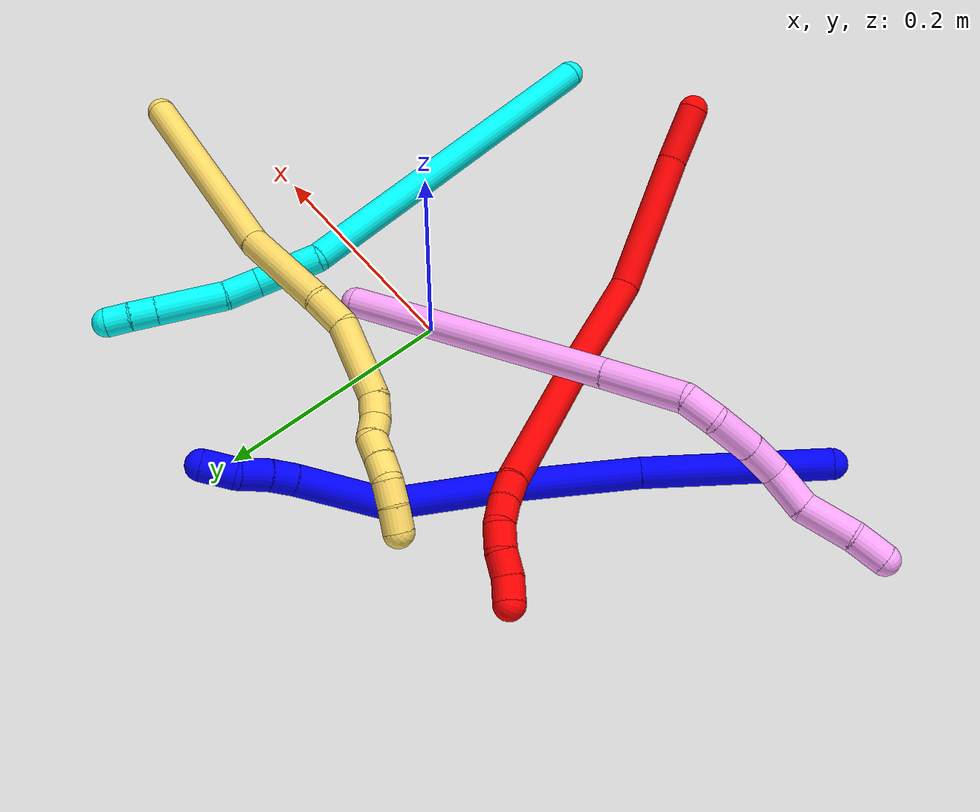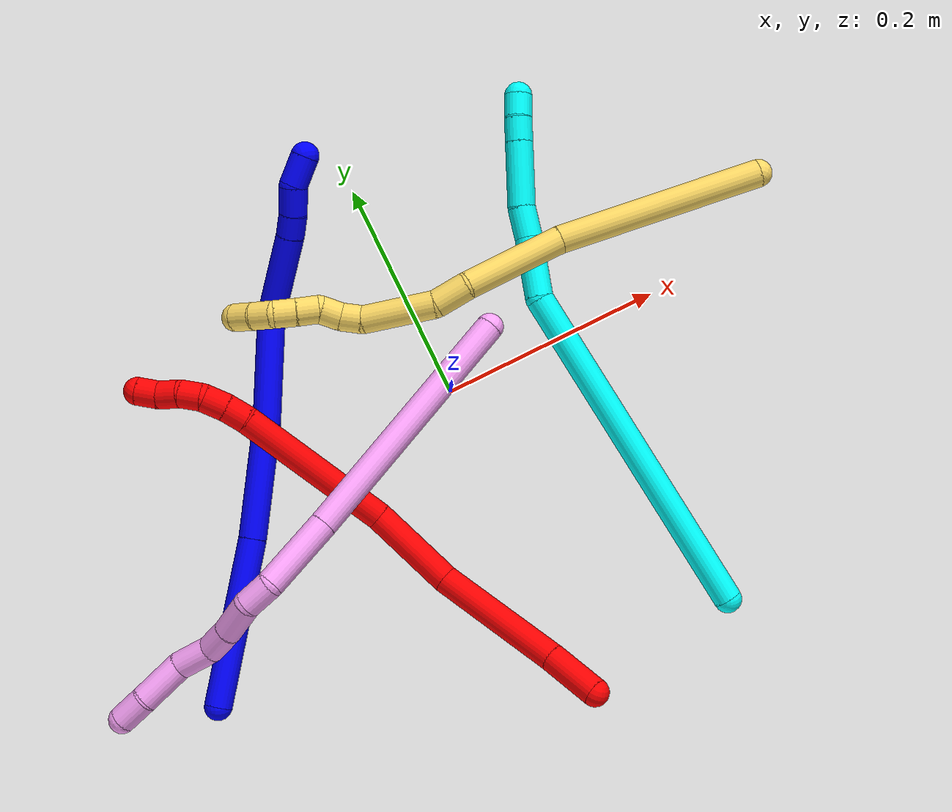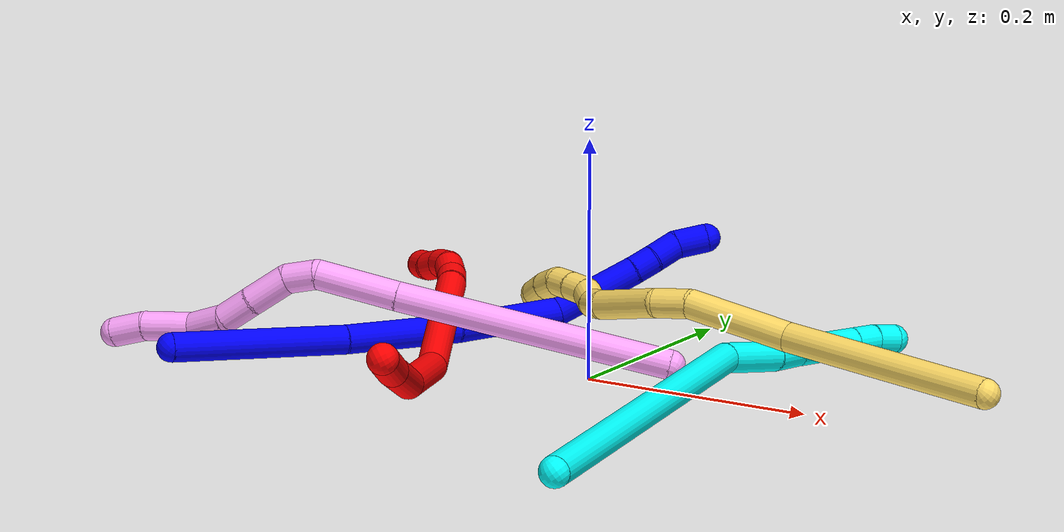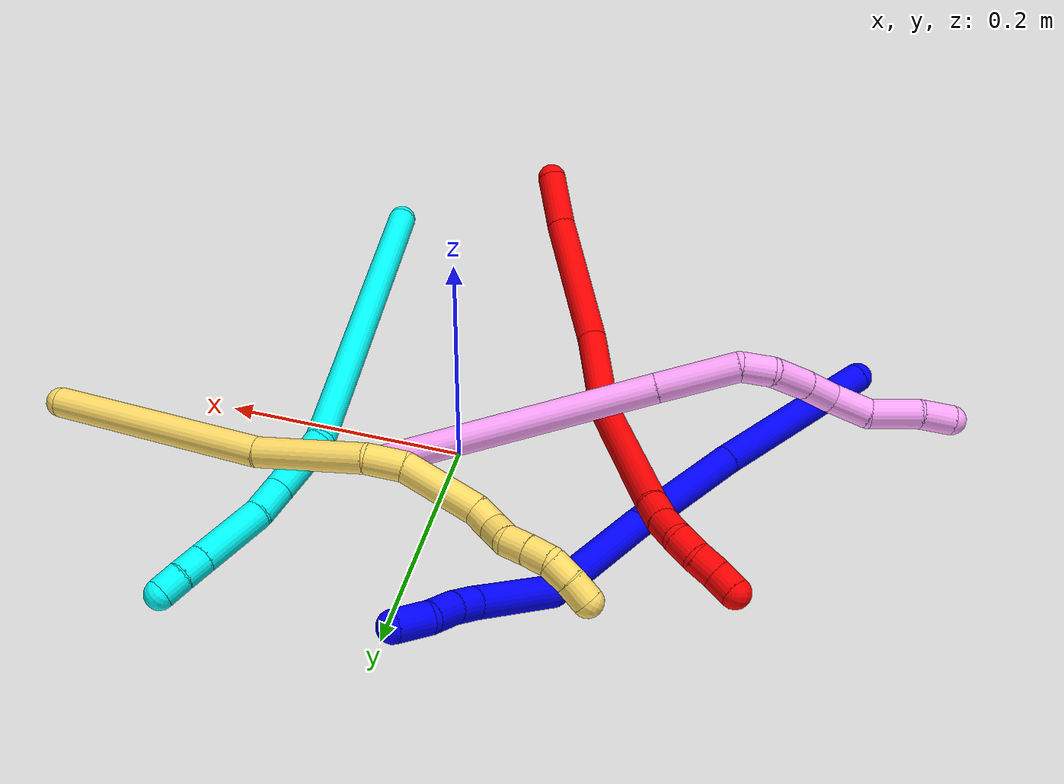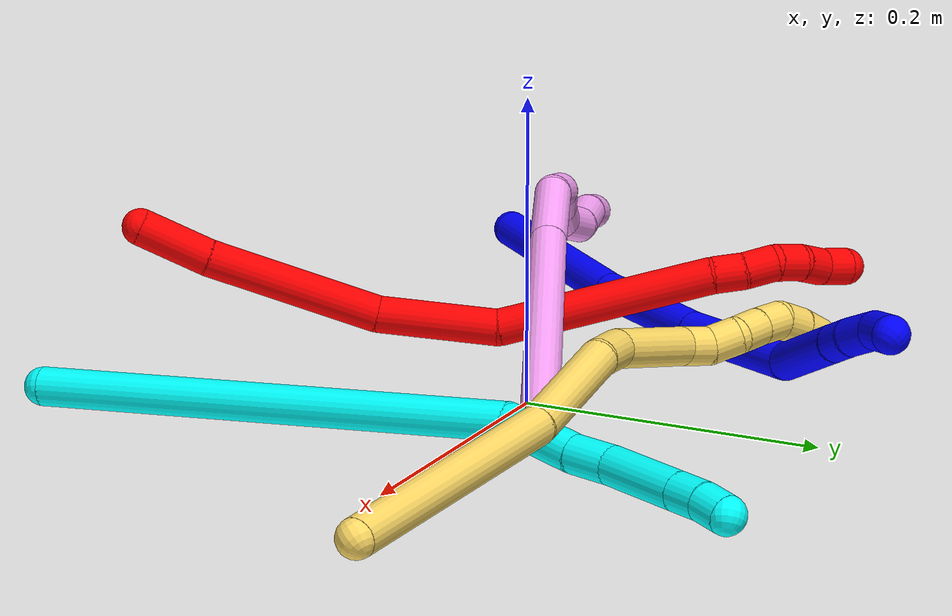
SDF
<sdf version="1.7">
 <world name="default">
  <plugin name="TubeGeneratorPlugin" filename="libtube_generator_plugin.so"/>
  <model name="photoneo_s_sensor">
   <static>1</static>
   <pose>0 0 2 1.57079 1.57079 3.14159</pose>
   <link name="link">
    <inertial><mass>0.1</mass></inertial>
    <sensor name="sensor" type="depth">
     <update_rate>30</update_rate>
     <camera>
      <horizontal_fov>1.22</horizontal_fov>
      <image><width>1920</width><height>1200</height><format>B8G8R8</format></image>
      <clip><near>0.1</near><far>4</far></clip>
      <depth_camera><output>points</output></depth_camera>
     </camera>
     <plugin name="camera_plugin" filename="libgazebo_ros_depth_camera.so">
      <baseline>0.2</baseline>
      <alwaysOn>1</alwaysOn>
      <updateRate>0.0</updateRate>
      <cameraName>camera_ir</cameraName>
      <imageTopicName>/camera/color/image_raw</imageTopicName>
      <cameraInfoTopicName>/camera/color/camera_info</cameraInfoTopicName>
      <depthImageTopicName>/camera/depth/image_raw</depthImageTopicName>
      <depthImageCameraInfoTopicName>/camera/depth/camera_info</depthImageCameraInfoTopicName>
      <pointCloudTopicName>/camera/depth/points</pointCloudTopicName>
      <frameName>fr_optical</frameName>
      <pointCloudCutoff>0.1</pointCloudCutoff>
      <pointCloudCutoffMax>2.0</pointCloudCutoffMax>
      <distortionK1>0</distortionK1>
      <distortionK2>0</distortionK2>
      <distortionK3>0</distortionK3>
      <distortionT1>0</distortionT1>
      <distortionT2>0</distortionT2>
      <CxPrime>0</CxPrime>
      <Cx>0</Cx>
      <Cy>0</Cy>
      <focalLength>0</focalLength>
      <hackBaseline>0</hackBaseline>
     </plugin>
    </sensor>
   </link>
  </model>
  <gravity>0 0 -9.8</gravity>
  <magnetic_field>6e-06 2.3e-05 -4.2e-05</magnetic_field>
  <atmosphere type="adiabatic"/>
  <physics name="default_physics" default="0" type="ode">
   <max_step_size>0.003</max_step_size>
   <real_time_factor>1</real_time_factor>
   <real_time_update_rate>1000</real_time_update_rate>
   <max_contacts>10000</max_contacts>
   <ode>
    <solver>
     <type>quick</type>
     <iters>100</iters>
     <sor>1.3</sor>
     <use_dynamic_moi_rescaling>0</use_dynamic_moi_rescaling>
    </solver>
    <constraints>
     <contact_max_correcting_vel>0</contact_max_correcting_vel>
     <contact_surface_layer>0.001</contact_surface_layer>
     <cfm>0</cfm>
     <erp>0.2</erp>
    </constraints>
   </ode>
  </physics>
  <scene><ambient>0.4 0.4 0.4 1</ambient><background>0.7 0.7 0.7 1</background><shadows>0</shadows></scene>
  <audio><device>default</device></audio>
  <spherical_coordinates>
   <surface_model>EARTH_WGS84</surface_model>
   <latitude_deg>0</latitude_deg>
   <longitude_deg>0</longitude_deg>
   <elevation>0</elevation>
   <heading_deg>0</heading_deg>
  </spherical_coordinates>
  <model name="bin">
   <static>1</static>
   <link name="bottom">
    <collision name="collision-bottom">
     <pose>0 0 -0.01 0 -0 0</pose>
     <geometry><box><size>0.8 0.6 0.02</size></box></geometry>
     <surface>
      <friction><ode><mu>100</mu><mu2>100</mu2></ode></friction>
      <contact><collide_bitmask>65535</collide_bitmask></contact>
     </surface>
    </collision>
   </link>
   <link name="west_wall">
    <collision name="collision-west_wall">
     <pose>-0.41 0 0.1 0 -0 0</pose>
     <geometry><box><size>0.02 0.6 0.2</size></box></geometry>
     <surface>
      <friction><ode><mu>100</mu><mu2>100</mu2></ode></friction>
      <contact><collide_bitmask>65535</collide_bitmask></contact>
     </surface>
    </collision>
   </link>
   <link name="east_wall">
    <collision name="collision-east_wall">
     <pose>0.41 0 0.1 0 -0 0</pose>
     <geometry><box><size>0.02 0.6 0.2</size></box></geometry>
     <surface>
      <friction><ode><mu>100</mu><mu2>100</mu2></ode></friction>
      <contact><collide_bitmask>65535</collide_bitmask></contact>
     </surface>
    </collision>
   </link>
   <link name="south_wall">
    <collision name="collision-south_wall">
     <pose>0 -0.31 0.1 0 -0 0</pose>
     <geometry><box><size>0.8 0.02 0.2</size></box></geometry>
     <surface>
      <friction><ode><mu>100</mu><mu2>100</mu2></ode></friction>
      <contact><collide_bitmask>65535</collide_bitmask></contact>
     </surface>
    </collision>
   </link>
   <link name="north_wall">
    <collision name="collision-north_wall">
     <pose>0 0.31 0.1 0 -0 0</pose>
     <geometry><box><size>0.8 0.02 0.2</size></box></geometry>
     <surface>
      <friction><ode><mu>100</mu><mu2>100</mu2></ode></friction>
      <contact><collide_bitmask>65535</collide_bitmask></contact>
     </surface>
    </collision>
   </link>
  </model>
  <model name="1">
   <static>0</static>
   <link name="1">
    <collision name="collision-cylinder-e_1_1_4">
     <pose>0.03828 0.058391 -0.028003 -2.01797 0.533859 -0.81964</pose>
     <geometry><cylinder><radius>0.0125</radius><length>0.150453</length></cylinder></geometry>
     <surface>
      <friction><ode><mu>1.16</mu><mu2>1.16</mu2><slip1>0</slip1><slip2>0</slip2></ode></friction>
      <contact><ode><kp>1e+06</kp><kd>1</kd><max_vel>0</max_vel><min_depth>0.001</min_depth></ode></contact>
     </surface>
    </collision>
    <visual name="visual-cylinder-e_1_1_4">
     <pose>0.03828 0.058391 -0.028003 -2.01797 0.533859 -0.81964</pose>
     <geometry><cylinder><radius>0.0125</radius><length>0.150453</length></cylinder></geometry>
     <material><ambient>0 0 1 1</ambient></material>
    </visual>
    <collision name="collision-cylinder-e_2_4_5">
     <pose>0.102818 0.158093 -0.071095 -1.92101 0.538263 -0.751334</pose>
     <geometry><cylinder><radius>0.0125</radius><length>0.102445</length></cylinder></geometry>
     <surface>
      <friction><ode><mu>1.16</mu><mu2>1.16</mu2><slip1>0</slip1><slip2>0</slip2></ode></friction>
      <contact><ode><kp>1e+06</kp><kd>1</kd><max_vel>0</max_vel><min_depth>0.001</min_depth></ode></contact>
     </surface>
    </collision>
    <visual name="visual-cylinder-e_2_4_5">
     <pose>0.102818 0.158093 -0.071095 -1.92101 0.538263 -0.751334</pose>
     <geometry><cylinder><radius>0.0125</radius><length>0.102445</length></cylinder></geometry>
     <material><ambient>0 0 1 1</ambient></material>
    </visual>
    <collision name="collision-cylinder-e_3_5_6">
     <pose>0.154561 0.239701 -0.096542 -1.82239 0.549535 -0.697339</pose>
     <geometry><cylinder><radius>0.0125</radius><length>0.097584</length></cylinder></geometry>
     <surface>
      <friction><ode><mu>1.16</mu><mu2>1.16</mu2><slip1>0</slip1><slip2>0</slip2></ode></friction>
      <contact><ode><kp>1e+06</kp><kd>1</kd><max_vel>0</max_vel><min_depth>0.001</min_depth></ode></contact>
     </surface>
    </collision>
    <visual name="visual-cylinder-e_3_5_6">
     <pose>0.154561 0.239701 -0.096542 -1.82239 0.549535 -0.697339</pose>
     <geometry><cylinder><radius>0.0125</radius><length>0.097584</length></cylinder></geometry>
     <material><ambient>0 0 1 1</ambient></material>
    </visual>
    <collision name="collision-cylinder-e_4_6_7">
     <pose>0.212445 0.29921 -0.113134 -1.88454 1.01339 -1.30429</pose>
     <geometry><cylinder><radius>0.0125</radius><length>0.076358</length></cylinder></geometry>
     <surface>
      <friction><ode><mu>1.16</mu><mu2>1.16</mu2><slip1>0</slip1><slip2>0</slip2></ode></friction>
      <contact><ode><kp>1e+06</kp><kd>1</kd><max_vel>0</max_vel><min_depth>0.001</min_depth></ode></contact>
     </surface>
    </collision>
    <visual name="visual-cylinder-e_4_6_7">
     <pose>0.212445 0.29921 -0.113134 -1.88454 1.01339 -1.30429</pose>
     <geometry><cylinder><radius>0.0125</radius><length>0.076358</length></cylinder></geometry>
     <material><ambient>0 0 1 1</ambient></material>
    </visual>
    <collision name="collision-cylinder-e_5_7_8">
     <pose>0.253364 0.324023 -0.120233 -1.72413 0.983615 -1.117</pose>
     <geometry><cylinder><radius>0.0125</radius><length>0.020467</length></cylinder></geometry>
     <surface>
      <friction><ode><mu>1.16</mu><mu2>1.16</mu2><slip1>0</slip1><slip2>0</slip2></ode></friction>
      <contact><ode><kp>1e+06</kp><kd>1</kd><max_vel>0</max_vel><min_depth>0.001</min_depth></ode></contact>
     </surface>
    </collision>
    <visual name="visual-cylinder-e_5_7_8">
     <pose>0.253364 0.324023 -0.120233 -1.72413 0.983615 -1.117</pose>
     <geometry><cylinder><radius>0.0125</radius><length>0.020467</length></cylinder></geometry>
     <material><ambient>0 0 1 1</ambient></material>
    </visual>
    <collision name="collision-cylinder-e_6_8_9">
     <pose>0.27154 0.337595 -0.121032 -1.56241 0.880875 -0.874421</pose>
     <geometry><cylinder><radius>0.0125</radius><length>0.025041</length></cylinder></geometry>
     <surface>
      <friction><ode><mu>1.16</mu><mu2>1.16</mu2><slip1>0</slip1><slip2>0</slip2></ode></friction>
      <contact><ode><kp>1e+06</kp><kd>1</kd><max_vel>0</max_vel><min_depth>0.001</min_depth></ode></contact>
     </surface>
    </collision>
    <visual name="visual-cylinder-e_6_8_9">
     <pose>0.27154 0.337595 -0.121032 -1.56241 0.880875 -0.874421</pose>
     <geometry><cylinder><radius>0.0125</radius><length>0.025041</length></cylinder></geometry>
     <material><ambient>0 0 1 1</ambient></material>
    </visual>
    <collision name="collision-cylinder-e_7_9_2">
     <pose>0.291209 0.35335 -0.126469 -2.18604 0.809761 -1.38278</pose>
     <geometry><cylinder><radius>0.0125</radius><length>0.027652</length></cylinder></geometry>
     <surface>
      <friction><ode><mu>1.16</mu><mu2>1.16</mu2><slip1>0</slip1><slip2>0</slip2></ode></friction>
      <contact><ode><kp>1e+06</kp><kd>1</kd><max_vel>0</max_vel><min_depth>0.001</min_depth></ode></contact>
     </surface>
    </collision>
    <visual name="visual-cylinder-e_7_9_2">
     <pose>0.291209 0.35335 -0.126469 -2.18604 0.809761 -1.38278</pose>
     <geometry><cylinder><radius>0.0125</radius><length>0.027652</length></cylinder></geometry>
     <material><ambient>0 0 1 1</ambient></material>
    </visual>
    <collision name="collision-sphere-2">
     <pose>0.30122 0.361137 -0.131972 0 -0 0</pose>
     <geometry><sphere><radius>0.0125</radius></sphere></geometry>
     <surface>
      <friction><ode><mu>1.16</mu><mu2>1.16</mu2><slip1>0</slip1><slip2>0</slip2></ode></friction>
      <contact><ode><kp>1e+06</kp><kd>1</kd><max_vel>0</max_vel><min_depth>0.001</min_depth></ode></contact>
     </surface>
    </collision>
    <visual name="visual-sphere-2">
     <pose>0.30122 0.361137 -0.131972 0 -0 0</pose>
     <geometry><sphere><radius>0.0125</radius></sphere></geometry>
     <material><ambient>0 0 1 1</ambient></material>
    </visual>
    <collision name="collision-sphere-9">
     <pose>0.281197 0.345563 -0.120965 0 -0 0</pose>
     <geometry><sphere><radius>0.0125</radius></sphere></geometry>
     <surface>
      <friction><ode><mu>1.16</mu><mu2>1.16</mu2><slip1>0</slip1><slip2>0</slip2></ode></friction>
      <contact><ode><kp>1e+06</kp><kd>1</kd><max_vel>0</max_vel><min_depth>0.001</min_depth></ode></contact>
     </surface>
    </collision>
    <visual name="visual-sphere-9">
     <pose>0.281197 0.345563 -0.120965 0 -0 0</pose>
     <geometry><sphere><radius>0.0125</radius></sphere></geometry>
     <material><ambient>0 0 1 1</ambient></material>
    </visual>
    <collision name="collision-sphere-4">
     <pose>0.076559 0.116782 -0.056006 0 -0 0</pose>
     <geometry><sphere><radius>0.0125</radius></sphere></geometry>
     <surface>
      <friction><ode><mu>1.16</mu><mu2>1.16</mu2><slip1>0</slip1><slip2>0</slip2></ode></friction>
      <contact><ode><kp>1e+06</kp><kd>1</kd><max_vel>0</max_vel><min_depth>0.001</min_depth></ode></contact>
     </surface>
    </collision>
    <visual name="visual-sphere-4">
     <pose>0.076559 0.116782 -0.056006 0 -0 0</pose>
     <geometry><sphere><radius>0.0125</radius></sphere></geometry>
     <material><ambient>0 0 1 1</ambient></material>
    </visual>
    <collision name="collision-sphere-1">
     <geometry><sphere><radius>0.0125</radius></sphere></geometry>
     <surface>
      <friction><ode><mu>1.16</mu><mu2>1.16</mu2><slip1>0</slip1><slip2>0</slip2></ode></friction>
      <contact><ode><kp>1e+06</kp><kd>1</kd><max_vel>0</max_vel><min_depth>0.001</min_depth></ode></contact>
     </surface>
    </collision>
    <visual name="visual-sphere-1">
     <geometry><sphere><radius>0.0125</radius></sphere></geometry>
     <material><ambient>0 0 1 1</ambient></material>
    </visual>
    <collision name="collision-sphere-8">
     <pose>0.261883 0.329626 -0.121099 0 -0 0</pose>
     <geometry><sphere><radius>0.0125</radius></sphere></geometry>
     <surface>
      <friction><ode><mu>1.16</mu><mu2>1.16</mu2><slip1>0</slip1><slip2>0</slip2></ode></friction>
      <contact><ode><kp>1e+06</kp><kd>1</kd><max_vel>0</max_vel><min_depth>0.001</min_depth></ode></contact>
     </surface>
    </collision>
    <visual name="visual-sphere-8">
     <pose>0.261883 0.329626 -0.121099 0 -0 0</pose>
     <geometry><sphere><radius>0.0125</radius></sphere></geometry>
     <material><ambient>0 0 1 1</ambient></material>
    </visual>
    <collision name="collision-sphere-5">
     <pose>0.129077 0.199403 -0.086184 0 -0 0</pose>
     <geometry><sphere><radius>0.0125</radius></sphere></geometry>
     <surface>
      <friction><ode><mu>1.16</mu><mu2>1.16</mu2><slip1>0</slip1><slip2>0</slip2></ode></friction>
      <contact><ode><kp>1e+06</kp><kd>1</kd><max_vel>0</max_vel><min_depth>0.001</min_depth></ode></contact>
     </surface>
    </collision>
    <visual name="visual-sphere-5">
     <pose>0.129077 0.199403 -0.086184 0 -0 0</pose>
     <geometry><sphere><radius>0.0125</radius></sphere></geometry>
     <material><ambient>0 0 1 1</ambient></material>
    </visual>
    <collision name="collision-sphere-6">
     <pose>0.180045 0.279999 -0.106901 0 -0 0</pose>
     <geometry><sphere><radius>0.0125</radius></sphere></geometry>
     <surface>
      <friction><ode><mu>1.16</mu><mu2>1.16</mu2><slip1>0</slip1><slip2>0</slip2></ode></friction>
      <contact><ode><kp>1e+06</kp><kd>1</kd><max_vel>0</max_vel><min_depth>0.001</min_depth></ode></contact>
     </surface>
    </collision>
    <visual name="visual-sphere-6">
     <pose>0.180045 0.279999 -0.106901 0 -0 0</pose>
     <geometry><sphere><radius>0.0125</radius></sphere></geometry>
     <material><ambient>0 0 1 1</ambient></material>
    </visual>
    <collision name="collision-sphere-7">
     <pose>0.244844 0.31842 -0.119367 0 -0 0</pose>
     <geometry><sphere><radius>0.0125</radius></sphere></geometry>
     <surface>
      <friction><ode><mu>1.16</mu><mu2>1.16</mu2><slip1>0</slip1><slip2>0</slip2></ode></friction>
      <contact><ode><kp>1e+06</kp><kd>1</kd><max_vel>0</max_vel><min_depth>0.001</min_depth></ode></contact>
     </surface>
    </collision>
    <visual name="visual-sphere-7">
     <pose>0.244844 0.31842 -0.119367 0 -0 0</pose>
     <geometry><sphere><radius>0.0125</radius></sphere></geometry>
     <material><ambient>0 0 1 1</ambient></material>
    </visual>
    <inertial>
     <pose>0.13527 0.192151 -0.07709 0 -0 0</pose>
     <mass>0.5</mass>
     <inertia>
      <ixx>7e-06</ixx>
      <ixy>0</ixy>
      <ixz>0</ixz>
      <iyy>-0.000216</iyy>
      <iyz>0</iyz>
      <izz>-0.000679</izz>
     </inertia>
    </inertial>
   </link>
   <pose>-0.30634 -0.160494 0.019296 -0.58669 -0.919383 0.465599</pose>
  </model>
  <model name="2">
   <static>0</static>
   <link name="2">
    <collision name="collision-cylinder-e_1_1_4">
     <pose>-0.020562 0.013727 -0.000702 -1.62192 -0.981553 1.02467</pose>
     <geometry><cylinder><radius>0.0125</radius><length>0.049465</length></cylinder></geometry>
     <surface>
      <friction><ode><mu>1.16</mu><mu2>1.16</mu2><slip1>0</slip1><slip2>0</slip2></ode></friction>
      <contact><ode><kp>1e+06</kp><kd>1</kd><max_vel>0</max_vel><min_depth>0.001</min_depth></ode></contact>
     </surface>
    </collision>
    <visual name="visual-cylinder-e_1_1_4">
     <pose>-0.020562 0.013727 -0.000702 -1.62192 -0.981553 1.02467</pose>
     <geometry><cylinder><radius>0.0125</radius><length>0.049465</length></cylinder></geometry>
     <material><ambient>1 0 0 1</ambient></material>
    </visual>
    <collision name="collision-cylinder-e_2_4_5">
     <pose>-0.086957 0.06549 -0.003598 -1.62838 -0.877277 0.922394</pose>
     <geometry><cylinder><radius>0.0125</radius><length>0.119203</length></cylinder></geometry>
     <surface>
      <friction><ode><mu>1.16</mu><mu2>1.16</mu2><slip1>0</slip1><slip2>0</slip2></ode></friction>
      <contact><ode><kp>1e+06</kp><kd>1</kd><max_vel>0</max_vel><min_depth>0.001</min_depth></ode></contact>
     </surface>
    </collision>
    <visual name="visual-cylinder-e_2_4_5">
     <pose>-0.086957 0.06549 -0.003598 -1.62838 -0.877277 0.922394</pose>
     <geometry><cylinder><radius>0.0125</radius><length>0.119203</length></cylinder></geometry>
     <material><ambient>1 0 0 1</ambient></material>
    </visual>
    <collision name="collision-cylinder-e_3_5_6">
     <pose>-0.158403 0.133188 -0.016882 -1.92865 -0.680102 0.943274</pose>
     <geometry><cylinder><radius>0.0125</radius><length>0.081457</length></cylinder></geometry>
     <surface>
      <friction><ode><mu>1.16</mu><mu2>1.16</mu2><slip1>0</slip1><slip2>0</slip2></ode></friction>
      <contact><ode><kp>1e+06</kp><kd>1</kd><max_vel>0</max_vel><min_depth>0.001</min_depth></ode></contact>
     </surface>
    </collision>
    <visual name="visual-cylinder-e_3_5_6">
     <pose>-0.158403 0.133188 -0.016882 -1.92865 -0.680102 0.943274</pose>
     <geometry><cylinder><radius>0.0125</radius><length>0.081457</length></cylinder></geometry>
     <material><ambient>1 0 0 1</ambient></material>
    </visual>
    <collision name="collision-cylinder-e_4_6_7">
     <pose>-0.207737 0.22831 -0.050944 -1.90827 -0.329459 0.460687</pose>
     <geometry><cylinder><radius>0.0125</radius><length>0.146635</length></cylinder></geometry>
     <surface>
      <friction><ode><mu>1.16</mu><mu2>1.16</mu2><slip1>0</slip1><slip2>0</slip2></ode></friction>
      <contact><ode><kp>1e+06</kp><kd>1</kd><max_vel>0</max_vel><min_depth>0.001</min_depth></ode></contact>
     </surface>
    </collision>
    <visual name="visual-cylinder-e_4_6_7">
     <pose>-0.207737 0.22831 -0.050944 -1.90827 -0.329459 0.460687</pose>
     <geometry><cylinder><radius>0.0125</radius><length>0.146635</length></cylinder></geometry>
     <material><ambient>1 0 0 1</ambient></material>
    </visual>
    <collision name="collision-cylinder-e_5_7_8">
     <pose>-0.235856 0.303175 -0.07568 -1.75633 -0.430888 0.515731</pose>
     <geometry><cylinder><radius>0.0125</radius><length>0.021062</length></cylinder></geometry>
     <surface>
      <friction><ode><mu>1.16</mu><mu2>1.16</mu2><slip1>0</slip1><slip2>0</slip2></ode></friction>
      <contact><ode><kp>1e+06</kp><kd>1</kd><max_vel>0</max_vel><min_depth>0.001</min_depth></ode></contact>
     </surface>
    </collision>
    <visual name="visual-cylinder-e_5_7_8">
     <pose>-0.235856 0.303175 -0.07568 -1.75633 -0.430888 0.515731</pose>
     <geometry><cylinder><radius>0.0125</radius><length>0.021062</length></cylinder></geometry>
     <material><ambient>1 0 0 1</ambient></material>
    </visual>
    <collision name="collision-cylinder-e_6_8_9">
     <pose>-0.243477 0.323062 -0.078456 -1.66694 -0.296985 0.326497</pose>
     <geometry><cylinder><radius>0.0125</radius><length>0.022027</length></cylinder></geometry>
     <surface>
      <friction><ode><mu>1.16</mu><mu2>1.16</mu2><slip1>0</slip1><slip2>0</slip2></ode></friction>
      <contact><ode><kp>1e+06</kp><kd>1</kd><max_vel>0</max_vel><min_depth>0.001</min_depth></ode></contact>
     </surface>
    </collision>
    <visual name="visual-cylinder-e_6_8_9">
     <pose>-0.243477 0.323062 -0.078456 -1.66694 -0.296985 0.326497</pose>
     <geometry><cylinder><radius>0.0125</radius><length>0.022027</length></cylinder></geometry>
     <material><ambient>1 0 0 1</ambient></material>
    </visual>
    <collision name="collision-cylinder-e_7_9_10">
     <pose>-0.25128 0.342049 -0.076861 -1.27337 -0.47548 0.354585</pose>
     <geometry><cylinder><radius>0.0125</radius><length>0.020008</length></cylinder></geometry>
     <surface>
      <friction><ode><mu>1.16</mu><mu2>1.16</mu2><slip1>0</slip1><slip2>0</slip2></ode></friction>
      <contact><ode><kp>1e+06</kp><kd>1</kd><max_vel>0</max_vel><min_depth>0.001</min_depth></ode></contact>
     </surface>
    </collision>
    <visual name="visual-cylinder-e_7_9_10">
     <pose>-0.25128 0.342049 -0.076861 -1.27337 -0.47548 0.354585</pose>
     <geometry><cylinder><radius>0.0125</radius><length>0.020008</length></cylinder></geometry>
     <material><ambient>1 0 0 1</ambient></material>
    </visual>
    <collision name="collision-cylinder-e_8_10_11">
     <pose>-0.260731 0.357749 -0.069184 -0.957041 -0.505462 0.266342</pose>
     <geometry><cylinder><radius>0.0125</radius><length>0.02012</length></cylinder></geometry>
     <surface>
      <friction><ode><mu>1.16</mu><mu2>1.16</mu2><slip1>0</slip1><slip2>0</slip2></ode></friction>
      <contact><ode><kp>1e+06</kp><kd>1</kd><max_vel>0</max_vel><min_depth>0.001</min_depth></ode></contact>
     </surface>
    </collision>
    <visual name="visual-cylinder-e_8_10_11">
     <pose>-0.260731 0.357749 -0.069184 -0.957041 -0.505462 0.266342</pose>
     <geometry><cylinder><radius>0.0125</radius><length>0.02012</length></cylinder></geometry>
     <material><ambient>1 0 0 1</ambient></material>
    </visual>
    <collision name="collision-cylinder-e_9_11_2">
     <pose>-0.270153 0.373501 -0.061606 -1.28555 -0.471914 0.356291</pose>
     <geometry><cylinder><radius>0.0125</radius><length>0.020022</length></cylinder></geometry>
     <surface>
      <friction><ode><mu>1.16</mu><mu2>1.16</mu2><slip1>0</slip1><slip2>0</slip2></ode></friction>
      <contact><ode><kp>1e+06</kp><kd>1</kd><max_vel>0</max_vel><min_depth>0.001</min_depth></ode></contact>
     </surface>
    </collision>
    <visual name="visual-cylinder-e_9_11_2">
     <pose>-0.270153 0.373501 -0.061606 -1.28555 -0.471914 0.356291</pose>
     <geometry><cylinder><radius>0.0125</radius><length>0.020022</length></cylinder></geometry>
     <material><ambient>1 0 0 1</ambient></material>
    </visual>
    <collision name="collision-sphere-2">
     <pose>-0.274704 0.382057 -0.059097 0 -0 0</pose>
     <geometry><sphere><radius>0.0125</radius></sphere></geometry>
     <surface>
      <friction><ode><mu>1.16</mu><mu2>1.16</mu2><slip1>0</slip1><slip2>0</slip2></ode></friction>
      <contact><ode><kp>1e+06</kp><kd>1</kd><max_vel>0</max_vel><min_depth>0.001</min_depth></ode></contact>
     </surface>
    </collision>
    <visual name="visual-sphere-2">
     <pose>-0.274704 0.382057 -0.059097 0 -0 0</pose>
     <geometry><sphere><radius>0.0125</radius></sphere></geometry>
     <material><ambient>1 0 0 1</ambient></material>
    </visual>
    <collision name="collision-sphere-11">
     <pose>-0.265602 0.364944 -0.064115 0 -0 0</pose>
     <geometry><sphere><radius>0.0125</radius></sphere></geometry>
     <surface>
      <friction><ode><mu>1.16</mu><mu2>1.16</mu2><slip1>0</slip1><slip2>0</slip2></ode></friction>
      <contact><ode><kp>1e+06</kp><kd>1</kd><max_vel>0</max_vel><min_depth>0.001</min_depth></ode></contact>
     </surface>
    </collision>
    <visual name="visual-sphere-11">
     <pose>-0.265602 0.364944 -0.064115 0 -0 0</pose>
     <geometry><sphere><radius>0.0125</radius></sphere></geometry>
     <material><ambient>1 0 0 1</ambient></material>
    </visual>
    <collision name="collision-sphere-10">
     <pose>-0.25586 0.350553 -0.074254 0 -0 0</pose>
     <geometry><sphere><radius>0.0125</radius></sphere></geometry>
     <surface>
      <friction><ode><mu>1.16</mu><mu2>1.16</mu2><slip1>0</slip1><slip2>0</slip2></ode></friction>
      <contact><ode><kp>1e+06</kp><kd>1</kd><max_vel>0</max_vel><min_depth>0.001</min_depth></ode></contact>
     </surface>
    </collision>
    <visual name="visual-sphere-10">
     <pose>-0.25586 0.350553 -0.074254 0 -0 0</pose>
     <geometry><sphere><radius>0.0125</radius></sphere></geometry>
     <material><ambient>1 0 0 1</ambient></material>
    </visual>
    <collision name="collision-sphere-9">
     <pose>-0.2467 0.333545 -0.079467 0 -0 0</pose>
     <geometry><sphere><radius>0.0125</radius></sphere></geometry>
     <surface>
      <friction><ode><mu>1.16</mu><mu2>1.16</mu2><slip1>0</slip1><slip2>0</slip2></ode></friction>
      <contact><ode><kp>1e+06</kp><kd>1</kd><max_vel>0</max_vel><min_depth>0.001</min_depth></ode></contact>
     </surface>
    </collision>
    <visual name="visual-sphere-9">
     <pose>-0.2467 0.333545 -0.079467 0 -0 0</pose>
     <geometry><sphere><radius>0.0125</radius></sphere></geometry>
     <material><ambient>1 0 0 1</ambient></material>
    </visual>
    <collision name="collision-sphere-4">
     <pose>-0.041123 0.027453 -0.001405 0 -0 0</pose>
     <geometry><sphere><radius>0.0125</radius></sphere></geometry>
     <surface>
      <friction><ode><mu>1.16</mu><mu2>1.16</mu2><slip1>0</slip1><slip2>0</slip2></ode></friction>
      <contact><ode><kp>1e+06</kp><kd>1</kd><max_vel>0</max_vel><min_depth>0.001</min_depth></ode></contact>
     </surface>
    </collision>
    <visual name="visual-sphere-4">
     <pose>-0.041123 0.027453 -0.001405 0 -0 0</pose>
     <geometry><sphere><radius>0.0125</radius></sphere></geometry>
     <material><ambient>1 0 0 1</ambient></material>
    </visual>
    <collision name="collision-sphere-1">
     <geometry><sphere><radius>0.0125</radius></sphere></geometry>
     <surface>
      <friction><ode><mu>1.16</mu><mu2>1.16</mu2><slip1>0</slip1><slip2>0</slip2></ode></friction>
      <contact><ode><kp>1e+06</kp><kd>1</kd><max_vel>0</max_vel><min_depth>0.001</min_depth></ode></contact>
     </surface>
    </collision>
    <visual name="visual-sphere-1">
     <geometry><sphere><radius>0.0125</radius></sphere></geometry>
     <material><ambient>1 0 0 1</ambient></material>
    </visual>
    <collision name="collision-sphere-8">
     <pose>-0.240254 0.312579 -0.077445 0 -0 0</pose>
     <geometry><sphere><radius>0.0125</radius></sphere></geometry>
     <surface>
      <friction><ode><mu>1.16</mu><mu2>1.16</mu2><slip1>0</slip1><slip2>0</slip2></ode></friction>
      <contact><ode><kp>1e+06</kp><kd>1</kd><max_vel>0</max_vel><min_depth>0.001</min_depth></ode></contact>
     </surface>
    </collision>
    <visual name="visual-sphere-8">
     <pose>-0.240254 0.312579 -0.077445 0 -0 0</pose>
     <geometry><sphere><radius>0.0125</radius></sphere></geometry>
     <material><ambient>1 0 0 1</ambient></material>
    </visual>
    <collision name="collision-sphere-5">
     <pose>-0.13279 0.103527 -0.00579 0 -0 0</pose>
     <geometry><sphere><radius>0.0125</radius></sphere></geometry>
     <surface>
      <friction><ode><mu>1.16</mu><mu2>1.16</mu2><slip1>0</slip1><slip2>0</slip2></ode></friction>
      <contact><ode><kp>1e+06</kp><kd>1</kd><max_vel>0</max_vel><min_depth>0.001</min_depth></ode></contact>
     </surface>
    </collision>
    <visual name="visual-sphere-5">
     <pose>-0.13279 0.103527 -0.00579 0 -0 0</pose>
     <geometry><sphere><radius>0.0125</radius></sphere></geometry>
     <material><ambient>1 0 0 1</ambient></material>
    </visual>
    <collision name="collision-sphere-6">
     <pose>-0.184016 0.162848 -0.027974 0 -0 0</pose>
     <geometry><sphere><radius>0.0125</radius></sphere></geometry>
     <surface>
      <friction><ode><mu>1.16</mu><mu2>1.16</mu2><slip1>0</slip1><slip2>0</slip2></ode></friction>
      <contact><ode><kp>1e+06</kp><kd>1</kd><max_vel>0</max_vel><min_depth>0.001</min_depth></ode></contact>
     </surface>
    </collision>
    <visual name="visual-sphere-6">
     <pose>-0.184016 0.162848 -0.027974 0 -0 0</pose>
     <geometry><sphere><radius>0.0125</radius></sphere></geometry>
     <material><ambient>1 0 0 1</ambient></material>
    </visual>
    <collision name="collision-sphere-7">
     <pose>-0.231457 0.293771 -0.073915 0 -0 0</pose>
     <geometry><sphere><radius>0.0125</radius></sphere></geometry>
     <surface>
      <friction><ode><mu>1.16</mu><mu2>1.16</mu2><slip1>0</slip1><slip2>0</slip2></ode></friction>
      <contact><ode><kp>1e+06</kp><kd>1</kd><max_vel>0</max_vel><min_depth>0.001</min_depth></ode></contact>
     </surface>
    </collision>
    <visual name="visual-sphere-7">
     <pose>-0.231457 0.293771 -0.073915 0 -0 0</pose>
     <geometry><sphere><radius>0.0125</radius></sphere></geometry>
     <material><ambient>1 0 0 1</ambient></material>
    </visual>
    <inertial>
     <pose>-0.161521 0.175669 -0.033589 0 -0 0</pose>
     <mass>0.5</mass>
     <inertia>
      <ixx>0.00052</ixx>
      <ixy>0</ixy>
      <ixz>0</ixz>
      <iyy>0.00032</iyy>
      <iyz>0</iyz>
      <izz>-0.000143</izz>
     </inertia>
    </inertial>
   </link>
   <pose>-0.00393 -0.286789 0.079909 2.38506 -0.928891 -1.55716</pose>
  </model>
  <model name="3">
   <static>0</static>
   <link name="3">
    <collision name="collision-cylinder-e_1_1_4">
     <pose>0.044024 0.150426 0.010958 -1.49808 0.283998 -0.264301</pose>
     <geometry><cylinder><radius>0.0125</radius><length>0.314236</length></cylinder></geometry>
     <surface>
      <friction><ode><mu>1.16</mu><mu2>1.16</mu2><slip1>0</slip1><slip2>0</slip2></ode></friction>
      <contact><ode><kp>1e+06</kp><kd>1</kd><max_vel>0</max_vel><min_depth>0.001</min_depth></ode></contact>
     </surface>
    </collision>
    <visual name="visual-cylinder-e_1_1_4">
     <pose>0.044024 0.150426 0.010958 -1.49808 0.283998 -0.264301</pose>
     <geometry><cylinder><radius>0.0125</radius><length>0.314236</length></cylinder></geometry>
     <material><ambient>0.003922 1 0.996078 1</ambient></material>
    </visual>
    <collision name="collision-cylinder-e_2_4_5">
     <pose>0.089512 0.325736 0.034073 -1.11638 0.052827 -0.032992</pose>
     <geometry><cylinder><radius>0.0125</radius><length>0.055469</length></cylinder></geometry>
     <surface>
      <friction><ode><mu>1.16</mu><mu2>1.16</mu2><slip1>0</slip1><slip2>0</slip2></ode></friction>
      <contact><ode><kp>1e+06</kp><kd>1</kd><max_vel>0</max_vel><min_depth>0.001</min_depth></ode></contact>
     </surface>
    </collision>
    <visual name="visual-cylinder-e_2_4_5">
     <pose>0.089512 0.325736 0.034073 -1.11638 0.052827 -0.032992</pose>
     <geometry><cylinder><radius>0.0125</radius><length>0.055469</length></cylinder></geometry>
     <material><ambient>0.003922 1 0.996078 1</ambient></material>
    </visual>
    <collision name="collision-cylinder-e_3_5_6">
     <pose>0.091685 0.364278 0.050867 -1.24347 0.049099 -0.035185</pose>
     <geometry><cylinder><radius>0.0125</radius><length>0.028879</length></cylinder></geometry>
     <surface>
      <friction><ode><mu>1.16</mu><mu2>1.16</mu2><slip1>0</slip1><slip2>0</slip2></ode></friction>
      <contact><ode><kp>1e+06</kp><kd>1</kd><max_vel>0</max_vel><min_depth>0.001</min_depth></ode></contact>
     </surface>
    </collision>
    <visual name="visual-cylinder-e_3_5_6">
     <pose>0.091685 0.364278 0.050867 -1.24347 0.049099 -0.035185</pose>
     <geometry><cylinder><radius>0.0125</radius><length>0.028879</length></cylinder></geometry>
     <material><ambient>0.003922 1 0.996078 1</ambient></material>
    </visual>
    <collision name="collision-cylinder-e_4_6_7">
     <pose>0.088786 0.404669 0.067197 -1.15848 -0.123019 0.080523</pose>
     <geometry><cylinder><radius>0.0125</radius><length>0.058805</length></cylinder></geometry>
     <surface>
      <friction><ode><mu>1.16</mu><mu2>1.16</mu2><slip1>0</slip1><slip2>0</slip2></ode></friction>
      <contact><ode><kp>1e+06</kp><kd>1</kd><max_vel>0</max_vel><min_depth>0.001</min_depth></ode></contact>
     </surface>
    </collision>
    <visual name="visual-cylinder-e_4_6_7">
     <pose>0.088786 0.404669 0.067197 -1.15848 -0.123019 0.080523</pose>
     <geometry><cylinder><radius>0.0125</radius><length>0.058805</length></cylinder></geometry>
     <material><ambient>0.003922 1 0.996078 1</ambient></material>
    </visual>
    <collision name="collision-cylinder-e_5_7_8">
     <pose>0.083814 0.441418 0.08326 -1.15937 -0.124151 0.081344</pose>
     <geometry><cylinder><radius>0.0125</radius><length>0.022021</length></cylinder></geometry>
     <surface>
      <friction><ode><mu>1.16</mu><mu2>1.16</mu2><slip1>0</slip1><slip2>0</slip2></ode></friction>
      <contact><ode><kp>1e+06</kp><kd>1</kd><max_vel>0</max_vel><min_depth>0.001</min_depth></ode></contact>
     </surface>
    </collision>
    <visual name="visual-cylinder-e_5_7_8">
     <pose>0.083814 0.441418 0.08326 -1.15937 -0.124151 0.081344</pose>
     <geometry><cylinder><radius>0.0125</radius><length>0.022021</length></cylinder></geometry>
     <material><ambient>0.003922 1 0.996078 1</ambient></material>
    </visual>
    <collision name="collision-cylinder-e_6_8_2">
     <pose>0.081372 0.460269 0.092799 -1.04147 -0.105033 0.060278</pose>
     <geometry><cylinder><radius>0.0125</radius><length>0.02059</length></cylinder></geometry>
     <surface>
      <friction><ode><mu>1.16</mu><mu2>1.16</mu2><slip1>0</slip1><slip2>0</slip2></ode></friction>
      <contact><ode><kp>1e+06</kp><kd>1</kd><max_vel>0</max_vel><min_depth>0.001</min_depth></ode></contact>
     </surface>
    </collision>
    <visual name="visual-cylinder-e_6_8_2">
     <pose>0.081372 0.460269 0.092799 -1.04147 -0.105033 0.060278</pose>
     <geometry><cylinder><radius>0.0125</radius><length>0.02059</length></cylinder></geometry>
     <material><ambient>0.003922 1 0.996078 1</ambient></material>
    </visual>
    <collision name="collision-sphere-2">
     <pose>0.080292 0.469106 0.097969 0 -0 0</pose>
     <geometry><sphere><radius>0.0125</radius></sphere></geometry>
     <surface>
      <friction><ode><mu>1.16</mu><mu2>1.16</mu2><slip1>0</slip1><slip2>0</slip2></ode></friction>
      <contact><ode><kp>1e+06</kp><kd>1</kd><max_vel>0</max_vel><min_depth>0.001</min_depth></ode></contact>
     </surface>
    </collision>
    <visual name="visual-sphere-2">
     <pose>0.080292 0.469106 0.097969 0 -0 0</pose>
     <geometry><sphere><radius>0.0125</radius></sphere></geometry>
     <material><ambient>0.003922 1 0.996078 1</ambient></material>
    </visual>
    <collision name="collision-sphere-4">
     <pose>0.088047 0.300851 0.021916 0 -0 0</pose>
     <geometry><sphere><radius>0.0125</radius></sphere></geometry>
     <surface>
      <friction><ode><mu>1.16</mu><mu2>1.16</mu2><slip1>0</slip1><slip2>0</slip2></ode></friction>
      <contact><ode><kp>1e+06</kp><kd>1</kd><max_vel>0</max_vel><min_depth>0.001</min_depth></ode></contact>
     </surface>
    </collision>
    <visual name="visual-sphere-4">
     <pose>0.088047 0.300851 0.021916 0 -0 0</pose>
     <geometry><sphere><radius>0.0125</radius></sphere></geometry>
     <material><ambient>0.003922 1 0.996078 1</ambient></material>
    </visual>
    <collision name="collision-sphere-1">
     <geometry><sphere><radius>0.0125</radius></sphere></geometry>
     <surface>
      <friction><ode><mu>1.16</mu><mu2>1.16</mu2><slip1>0</slip1><slip2>0</slip2></ode></friction>
      <contact><ode><kp>1e+06</kp><kd>1</kd><max_vel>0</max_vel><min_depth>0.001</min_depth></ode></contact>
     </surface>
    </collision>
    <visual name="visual-sphere-1">
     <geometry><sphere><radius>0.0125</radius></sphere></geometry>
     <material><ambient>0.003922 1 0.996078 1</ambient></material>
    </visual>
    <collision name="collision-sphere-8">
     <pose>0.082451 0.451432 0.087629 0 -0 0</pose>
     <geometry><sphere><radius>0.0125</radius></sphere></geometry>
     <surface>
      <friction><ode><mu>1.16</mu><mu2>1.16</mu2><slip1>0</slip1><slip2>0</slip2></ode></friction>
      <contact><ode><kp>1e+06</kp><kd>1</kd><max_vel>0</max_vel><min_depth>0.001</min_depth></ode></contact>
     </surface>
    </collision>
    <visual name="visual-sphere-8">
     <pose>0.082451 0.451432 0.087629 0 -0 0</pose>
     <geometry><sphere><radius>0.0125</radius></sphere></geometry>
     <material><ambient>0.003922 1 0.996078 1</ambient></material>
    </visual>
    <collision name="collision-sphere-5">
     <pose>0.090976 0.350621 0.04623 0 -0 0</pose>
     <geometry><sphere><radius>0.0125</radius></sphere></geometry>
     <surface>
      <friction><ode><mu>1.16</mu><mu2>1.16</mu2><slip1>0</slip1><slip2>0</slip2></ode></friction>
      <contact><ode><kp>1e+06</kp><kd>1</kd><max_vel>0</max_vel><min_depth>0.001</min_depth></ode></contact>
     </surface>
    </collision>
    <visual name="visual-sphere-5">
     <pose>0.090976 0.350621 0.04623 0 -0 0</pose>
     <geometry><sphere><radius>0.0125</radius></sphere></geometry>
     <material><ambient>0.003922 1 0.996078 1</ambient></material>
    </visual>
    <collision name="collision-sphere-6">
     <pose>0.092394 0.377934 0.055504 0 -0 0</pose>
     <geometry><sphere><radius>0.0125</radius></sphere></geometry>
     <surface>
      <friction><ode><mu>1.16</mu><mu2>1.16</mu2><slip1>0</slip1><slip2>0</slip2></ode></friction>
      <contact><ode><kp>1e+06</kp><kd>1</kd><max_vel>0</max_vel><min_depth>0.001</min_depth></ode></contact>
     </surface>
    </collision>
    <visual name="visual-sphere-6">
     <pose>0.092394 0.377934 0.055504 0 -0 0</pose>
     <geometry><sphere><radius>0.0125</radius></sphere></geometry>
     <material><ambient>0.003922 1 0.996078 1</ambient></material>
    </visual>
    <collision name="collision-sphere-7">
     <pose>0.085178 0.431404 0.07889 0 -0 0</pose>
     <geometry><sphere><radius>0.0125</radius></sphere></geometry>
     <surface>
      <friction><ode><mu>1.16</mu><mu2>1.16</mu2><slip1>0</slip1><slip2>0</slip2></ode></friction>
      <contact><ode><kp>1e+06</kp><kd>1</kd><max_vel>0</max_vel><min_depth>0.001</min_depth></ode></contact>
     </surface>
    </collision>
    <visual name="visual-sphere-7">
     <pose>0.085178 0.431404 0.07889 0 -0 0</pose>
     <geometry><sphere><radius>0.0125</radius></sphere></geometry>
     <material><ambient>0.003922 1 0.996078 1</ambient></material>
    </visual>
    <inertial>
     <pose>0.060378 0.237703 0.028996 0 -0 0</pose>
     <mass>0.5</mass>
     <inertia>
      <ixx>0.001805</ixx>
      <ixy>0</ixy>
      <ixz>0</ixz>
      <iyy>-0.000224</iyy>
      <iyz>0</iyz>
      <izz>-0.003244</izz>
     </inertia>
    </inertial>
   </link>
   <pose>0.139859 -0.273639 0.012015 2.82579 0.578745 2.87908</pose>
  </model>
  <model name="4">
   <static>0</static>
   <link name="4">
    <collision name="collision-cylinder-e_1_1_4">
     <pose>-0.113635 -0.020309 -0.01254 2.12395 -1.36376 -1.93749</pose>
     <geometry><cylinder><radius>0.0125</radius><length>0.23223</length></cylinder></geometry>
     <surface>
      <friction><ode><mu>1.16</mu><mu2>1.16</mu2><slip1>0</slip1><slip2>0</slip2></ode></friction>
      <contact><ode><kp>1e+06</kp><kd>1</kd><max_vel>0</max_vel><min_depth>0.001</min_depth></ode></contact>
     </surface>
    </collision>
    <visual name="visual-cylinder-e_1_1_4">
     <pose>-0.113635 -0.020309 -0.01254 2.12395 -1.36376 -1.93749</pose>
     <geometry><cylinder><radius>0.0125</radius><length>0.23223</length></cylinder></geometry>
     <material><ambient>1 0.65098 0.996078 1</ambient></material>
    </visual>
    <collision name="collision-cylinder-e_2_4_5">
     <pose>-0.26098 -0.046484 -0.029818 2.25024 -1.35075 -2.06607</pose>
     <geometry><cylinder><radius>0.0125</radius><length>0.069084</length></cylinder></geometry>
     <surface>
      <friction><ode><mu>1.16</mu><mu2>1.16</mu2><slip1>0</slip1><slip2>0</slip2></ode></friction>
      <contact><ode><kp>1e+06</kp><kd>1</kd><max_vel>0</max_vel><min_depth>0.001</min_depth></ode></contact>
     </surface>
    </collision>
    <visual name="visual-cylinder-e_2_4_5">
     <pose>-0.26098 -0.046484 -0.029818 2.25024 -1.35075 -2.06607</pose>
     <geometry><cylinder><radius>0.0125</radius><length>0.069084</length></cylinder></geometry>
     <material><ambient>1 0.65098 0.996078 1</ambient></material>
    </visual>
    <collision name="collision-cylinder-e_3_5_6">
     <pose>-0.305757 -0.060364 -0.035502 1.6883 -0.940772 -1.03916</pose>
     <geometry><cylinder><radius>0.0125</radius><length>0.027397</length></cylinder></geometry>
     <surface>
      <friction><ode><mu>1.16</mu><mu2>1.16</mu2><slip1>0</slip1><slip2>0</slip2></ode></friction>
      <contact><ode><kp>1e+06</kp><kd>1</kd><max_vel>0</max_vel><min_depth>0.001</min_depth></ode></contact>
     </surface>
    </collision>
    <visual name="visual-cylinder-e_3_5_6">
     <pose>-0.305757 -0.060364 -0.035502 1.6883 -0.940772 -1.03916</pose>
     <geometry><cylinder><radius>0.0125</radius><length>0.027397</length></cylinder></geometry>
     <material><ambient>1 0.65098 0.996078 1</ambient></material>
    </visual>
    <collision name="collision-cylinder-e_4_6_7">
     <pose>-0.327809 -0.082191 -0.031922 1.25419 -0.647093 -0.476768</pose>
     <geometry><cylinder><radius>0.0125</radius><length>0.036434</length></cylinder></geometry>
     <surface>
      <friction><ode><mu>1.16</mu><mu2>1.16</mu2><slip1>0</slip1><slip2>0</slip2></ode></friction>
      <contact><ode><kp>1e+06</kp><kd>1</kd><max_vel>0</max_vel><min_depth>0.001</min_depth></ode></contact>
     </surface>
    </collision>
    <visual name="visual-cylinder-e_4_6_7">
     <pose>-0.327809 -0.082191 -0.031922 1.25419 -0.647093 -0.476768</pose>
     <geometry><cylinder><radius>0.0125</radius><length>0.036434</length></cylinder></geometry>
     <material><ambient>1 0.65098 0.996078 1</ambient></material>
    </visual>
    <collision name="collision-cylinder-e_5_7_8">
     <pose>-0.347004 -0.107556 -0.02508 1.37281 -0.608682 -0.503757</pose>
     <geometry><cylinder><radius>0.0125</radius><length>0.028726</length></cylinder></geometry>
     <surface>
      <friction><ode><mu>1.16</mu><mu2>1.16</mu2><slip1>0</slip1><slip2>0</slip2></ode></friction>
      <contact><ode><kp>1e+06</kp><kd>1</kd><max_vel>0</max_vel><min_depth>0.001</min_depth></ode></contact>
     </surface>
    </collision>
    <visual name="visual-cylinder-e_5_7_8">
     <pose>-0.347004 -0.107556 -0.02508 1.37281 -0.608682 -0.503757</pose>
     <geometry><cylinder><radius>0.0125</radius><length>0.028726</length></cylinder></geometry>
     <material><ambient>1 0.65098 0.996078 1</ambient></material>
    </visual>
    <collision name="collision-cylinder-e_6_8_9">
     <pose>-0.366343 -0.131679 -0.026126 1.83232 -0.707462 -0.896816</pose>
     <geometry><cylinder><radius>0.0125</radius><length>0.034242</length></cylinder></geometry>
     <surface>
      <friction><ode><mu>1.16</mu><mu2>1.16</mu2><slip1>0</slip1><slip2>0</slip2></ode></friction>
      <contact><ode><kp>1e+06</kp><kd>1</kd><max_vel>0</max_vel><min_depth>0.001</min_depth></ode></contact>
     </surface>
    </collision>
    <visual name="visual-cylinder-e_6_8_9">
     <pose>-0.366343 -0.131679 -0.026126 1.83232 -0.707462 -0.896816</pose>
     <geometry><cylinder><radius>0.0125</radius><length>0.034242</length></cylinder></geometry>
     <material><ambient>1 0.65098 0.996078 1</ambient></material>
    </visual>
    <collision name="collision-cylinder-e_7_9_10">
     <pose>-0.39671 -0.153834 -0.031798 1.807 -1.09725 -1.3196</pose>
     <geometry><cylinder><radius>0.0125</radius><length>0.043237</length></cylinder></geometry>
     <surface>
      <friction><ode><mu>1.16</mu><mu2>1.16</mu2><slip1>0</slip1><slip2>0</slip2></ode></friction>
      <contact><ode><kp>1e+06</kp><kd>1</kd><max_vel>0</max_vel><min_depth>0.001</min_depth></ode></contact>
     </surface>
    </collision>
    <visual name="visual-cylinder-e_7_9_10">
     <pose>-0.39671 -0.153834 -0.031798 1.807 -1.09725 -1.3196</pose>
     <geometry><cylinder><radius>0.0125</radius><length>0.043237</length></cylinder></geometry>
     <material><ambient>1 0.65098 0.996078 1</ambient></material>
    </visual>
    <collision name="collision-cylinder-e_8_10_2">
     <pose>-0.427196 -0.172281 -0.03453 1.61878 -0.902879 -0.941121</pose>
     <geometry><cylinder><radius>0.0125</radius><length>0.02865</length></cylinder></geometry>
     <surface>
      <friction><ode><mu>1.16</mu><mu2>1.16</mu2><slip1>0</slip1><slip2>0</slip2></ode></friction>
      <contact><ode><kp>1e+06</kp><kd>1</kd><max_vel>0</max_vel><min_depth>0.001</min_depth></ode></contact>
     </surface>
    </collision>
    <visual name="visual-cylinder-e_8_10_2">
     <pose>-0.427196 -0.172281 -0.03453 1.61878 -0.902879 -0.941121</pose>
     <geometry><cylinder><radius>0.0125</radius><length>0.02865</length></cylinder></geometry>
     <material><ambient>1 0.65098 0.996078 1</ambient></material>
    </visual>
    <collision name="collision-sphere-2">
     <pose>-0.438443 -0.181143 -0.034956 0 -0 0</pose>
     <geometry><sphere><radius>0.0125</radius></sphere></geometry>
     <surface>
      <friction><ode><mu>1.16</mu><mu2>1.16</mu2><slip1>0</slip1><slip2>0</slip2></ode></friction>
      <contact><ode><kp>1e+06</kp><kd>1</kd><max_vel>0</max_vel><min_depth>0.001</min_depth></ode></contact>
     </surface>
    </collision>
    <visual name="visual-sphere-2">
     <pose>-0.438443 -0.181143 -0.034956 0 -0 0</pose>
     <geometry><sphere><radius>0.0125</radius></sphere></geometry>
     <material><ambient>1 0.65098 0.996078 1</ambient></material>
    </visual>
    <collision name="collision-sphere-10">
     <pose>-0.415949 -0.16342 -0.034105 0 -0 0</pose>
     <geometry><sphere><radius>0.0125</radius></sphere></geometry>
     <surface>
      <friction><ode><mu>1.16</mu><mu2>1.16</mu2><slip1>0</slip1><slip2>0</slip2></ode></friction>
      <contact><ode><kp>1e+06</kp><kd>1</kd><max_vel>0</max_vel><min_depth>0.001</min_depth></ode></contact>
     </surface>
    </collision>
    <visual name="visual-sphere-10">
     <pose>-0.415949 -0.16342 -0.034105 0 -0 0</pose>
     <geometry><sphere><radius>0.0125</radius></sphere></geometry>
     <material><ambient>1 0.65098 0.996078 1</ambient></material>
    </visual>
    <collision name="collision-sphere-9">
     <pose>-0.37747 -0.144249 -0.02949 0 -0 0</pose>
     <geometry><sphere><radius>0.0125</radius></sphere></geometry>
     <surface>
      <friction><ode><mu>1.16</mu><mu2>1.16</mu2><slip1>0</slip1><slip2>0</slip2></ode></friction>
      <contact><ode><kp>1e+06</kp><kd>1</kd><max_vel>0</max_vel><min_depth>0.001</min_depth></ode></contact>
     </surface>
    </collision>
    <visual name="visual-sphere-9">
     <pose>-0.37747 -0.144249 -0.02949 0 -0 0</pose>
     <geometry><sphere><radius>0.0125</radius></sphere></geometry>
     <material><ambient>1 0.65098 0.996078 1</ambient></material>
    </visual>
    <collision name="collision-sphere-4">
     <pose>-0.227271 -0.040619 -0.02508 0 -0 0</pose>
     <geometry><sphere><radius>0.0125</radius></sphere></geometry>
     <surface>
      <friction><ode><mu>1.16</mu><mu2>1.16</mu2><slip1>0</slip1><slip2>0</slip2></ode></friction>
      <contact><ode><kp>1e+06</kp><kd>1</kd><max_vel>0</max_vel><min_depth>0.001</min_depth></ode></contact>
     </surface>
    </collision>
    <visual name="visual-sphere-4">
     <pose>-0.227271 -0.040619 -0.02508 0 -0 0</pose>
     <geometry><sphere><radius>0.0125</radius></sphere></geometry>
     <material><ambient>1 0.65098 0.996078 1</ambient></material>
    </visual>
    <collision name="collision-sphere-1">
     <geometry><sphere><radius>0.0125</radius></sphere></geometry>
     <surface>
      <friction><ode><mu>1.16</mu><mu2>1.16</mu2><slip1>0</slip1><slip2>0</slip2></ode></friction>
      <contact><ode><kp>1e+06</kp><kd>1</kd><max_vel>0</max_vel><min_depth>0.001</min_depth></ode></contact>
     </surface>
    </collision>
    <visual name="visual-sphere-1">
     <geometry><sphere><radius>0.0125</radius></sphere></geometry>
     <material><ambient>1 0.65098 0.996078 1</ambient></material>
    </visual>
    <collision name="collision-sphere-8">
     <pose>-0.355216 -0.119109 -0.022762 0 -0 0</pose>
     <geometry><sphere><radius>0.0125</radius></sphere></geometry>
     <surface>
      <friction><ode><mu>1.16</mu><mu2>1.16</mu2><slip1>0</slip1><slip2>0</slip2></ode></friction>
      <contact><ode><kp>1e+06</kp><kd>1</kd><max_vel>0</max_vel><min_depth>0.001</min_depth></ode></contact>
     </surface>
    </collision>
    <visual name="visual-sphere-8">
     <pose>-0.355216 -0.119109 -0.022762 0 -0 0</pose>
     <geometry><sphere><radius>0.0125</radius></sphere></geometry>
     <material><ambient>1 0.65098 0.996078 1</ambient></material>
    </visual>
    <collision name="collision-sphere-5">
     <pose>-0.294689 -0.052349 -0.034555 0 -0 0</pose>
     <geometry><sphere><radius>0.0125</radius></sphere></geometry>
     <surface>
      <friction><ode><mu>1.16</mu><mu2>1.16</mu2><slip1>0</slip1><slip2>0</slip2></ode></friction>
      <contact><ode><kp>1e+06</kp><kd>1</kd><max_vel>0</max_vel><min_depth>0.001</min_depth></ode></contact>
     </surface>
    </collision>
    <visual name="visual-sphere-5">
     <pose>-0.294689 -0.052349 -0.034555 0 -0 0</pose>
     <geometry><sphere><radius>0.0125</radius></sphere></geometry>
     <material><ambient>1 0.65098 0.996078 1</ambient></material>
    </visual>
    <collision name="collision-sphere-6">
     <pose>-0.316826 -0.068379 -0.036448 0 -0 0</pose>
     <geometry><sphere><radius>0.0125</radius></sphere></geometry>
     <surface>
      <friction><ode><mu>1.16</mu><mu2>1.16</mu2><slip1>0</slip1><slip2>0</slip2></ode></friction>
      <contact><ode><kp>1e+06</kp><kd>1</kd><max_vel>0</max_vel><min_depth>0.001</min_depth></ode></contact>
     </surface>
    </collision>
    <visual name="visual-sphere-6">
     <pose>-0.316826 -0.068379 -0.036448 0 -0 0</pose>
     <geometry><sphere><radius>0.0125</radius></sphere></geometry>
     <material><ambient>1 0.65098 0.996078 1</ambient></material>
    </visual>
    <collision name="collision-sphere-7">
     <pose>-0.338791 -0.096003 -0.027397 0 -0 0</pose>
     <geometry><sphere><radius>0.0125</radius></sphere></geometry>
     <surface>
      <friction><ode><mu>1.16</mu><mu2>1.16</mu2><slip1>0</slip1><slip2>0</slip2></ode></friction>
      <contact><ode><kp>1e+06</kp><kd>1</kd><max_vel>0</max_vel><min_depth>0.001</min_depth></ode></contact>
     </surface>
    </collision>
    <visual name="visual-sphere-7">
     <pose>-0.338791 -0.096003 -0.027397 0 -0 0</pose>
     <geometry><sphere><radius>0.0125</radius></sphere></geometry>
     <material><ambient>1 0.65098 0.996078 1</ambient></material>
    </visual>
    <inertial>
     <pose>-0.233287 -0.063524 -0.022174 0 -0 0</pose>
     <mass>0.5</mass>
     <inertia>
      <ixx>-0.000324</ixx>
      <ixy>0</ixy>
      <ixz>0</ixz>
      <iyy>0.000827</iyy>
      <iyz>0</iyz>
      <izz>0.001284</izz>
     </inertia>
    </inertial>
   </link>
   <pose>0.056323 0.036171 0.012209 2.03516 0.329547 0.603828</pose>
  </model>
  <model name="5">
   <static>0</static>
   <link name="5">
    <collision name="collision-cylinder-e_1_1_4">
     <pose>-0.077607 -0.046594 0.026181 1.05886 -0.967711 -0.596662</pose>
     <geometry><cylinder><radius>0.0125</radius><length>0.188459</length></cylinder></geometry>
     <surface>
      <friction><ode><mu>1.16</mu><mu2>1.16</mu2><slip1>0</slip1><slip2>0</slip2></ode></friction>
      <contact><ode><kp>1e+06</kp><kd>1</kd><max_vel>0</max_vel><min_depth>0.001</min_depth></ode></contact>
     </surface>
    </collision>
    <visual name="visual-cylinder-e_1_1_4">
     <pose>-0.077607 -0.046594 0.026181 1.05886 -0.967711 -0.596662</pose>
     <geometry><cylinder><radius>0.0125</radius><length>0.188459</length></cylinder></geometry>
     <material><ambient>1 0.858824 0.4 1</ambient></material>
    </visual>
    <collision name="collision-cylinder-e_2_4_5">
     <pose>-0.190712 -0.115017 0.072735 0.819915 -0.87148 -0.399279</pose>
     <geometry><cylinder><radius>0.0125</radius><length>0.092772</length></cylinder></geometry>
     <surface>
      <friction><ode><mu>1.16</mu><mu2>1.16</mu2><slip1>0</slip1><slip2>0</slip2></ode></friction>
      <contact><ode><kp>1e+06</kp><kd>1</kd><max_vel>0</max_vel><min_depth>0.001</min_depth></ode></contact>
     </surface>
    </collision>
    <visual name="visual-cylinder-e_2_4_5">
     <pose>-0.190712 -0.115017 0.072735 0.819915 -0.87148 -0.399279</pose>
     <geometry><cylinder><radius>0.0125</radius><length>0.092772</length></cylinder></geometry>
     <material><ambient>1 0.858824 0.4 1</ambient></material>
    </visual>
    <collision name="collision-cylinder-e_3_5_6">
     <pose>-0.236616 -0.147687 0.098135 1.13649 -0.716425 -0.469252</pose>
     <geometry><cylinder><radius>0.0125</radius><length>0.031692</length></cylinder></geometry>
     <surface>
      <friction><ode><mu>1.16</mu><mu2>1.16</mu2><slip1>0</slip1><slip2>0</slip2></ode></friction>
      <contact><ode><kp>1e+06</kp><kd>1</kd><max_vel>0</max_vel><min_depth>0.001</min_depth></ode></contact>
     </surface>
    </collision>
    <visual name="visual-cylinder-e_3_5_6">
     <pose>-0.236616 -0.147687 0.098135 1.13649 -0.716425 -0.469252</pose>
     <geometry><cylinder><radius>0.0125</radius><length>0.031692</length></cylinder></geometry>
     <material><ambient>1 0.858824 0.4 1</ambient></material>
    </visual>
    <collision name="collision-cylinder-e_4_6_7">
     <pose>-0.272936 -0.179357 0.103038 1.57685 -0.893734 -0.898463</pose>
     <geometry><cylinder><radius>0.0125</radius><length>0.066494</length></cylinder></geometry>
     <surface>
      <friction><ode><mu>1.16</mu><mu2>1.16</mu2><slip1>0</slip1><slip2>0</slip2></ode></friction>
      <contact><ode><kp>1e+06</kp><kd>1</kd><max_vel>0</max_vel><min_depth>0.001</min_depth></ode></contact>
     </surface>
    </collision>
    <visual name="visual-cylinder-e_4_6_7">
     <pose>-0.272936 -0.179357 0.103038 1.57685 -0.893734 -0.898463</pose>
     <geometry><cylinder><radius>0.0125</radius><length>0.066494</length></cylinder></geometry>
     <material><ambient>1 0.858824 0.4 1</ambient></material>
    </visual>
    <collision name="collision-cylinder-e_5_7_8">
     <pose>-0.307829 -0.204264 0.10064 2.07897 -1.09146 -1.60354</pose>
     <geometry><cylinder><radius>0.0125</radius><length>0.020242</length></cylinder></geometry>
     <surface>
      <friction><ode><mu>1.16</mu><mu2>1.16</mu2><slip1>0</slip1><slip2>0</slip2></ode></friction>
      <contact><ode><kp>1e+06</kp><kd>1</kd><max_vel>0</max_vel><min_depth>0.001</min_depth></ode></contact>
     </surface>
    </collision>
    <visual name="visual-cylinder-e_5_7_8">
     <pose>-0.307829 -0.204264 0.10064 2.07897 -1.09146 -1.60354</pose>
     <geometry><cylinder><radius>0.0125</radius><length>0.020242</length></cylinder></geometry>
     <material><ambient>1 0.858824 0.4 1</ambient></material>
    </visual>
    <collision name="collision-cylinder-e_6_8_9">
     <pose>-0.326888 -0.20836 0.097172 3.12684 -1.45256 -3.12499</pose>
     <geometry><cylinder><radius>0.0125</radius><length>0.0203</length></cylinder></geometry>
     <surface>
      <friction><ode><mu>1.16</mu><mu2>1.16</mu2><slip1>0</slip1><slip2>0</slip2></ode></friction>
      <contact><ode><kp>1e+06</kp><kd>1</kd><max_vel>0</max_vel><min_depth>0.001</min_depth></ode></contact>
     </surface>
    </collision>
    <visual name="visual-cylinder-e_6_8_9">
     <pose>-0.326888 -0.20836 0.097172 3.12684 -1.45256 -3.12499</pose>
     <geometry><cylinder><radius>0.0125</radius><length>0.0203</length></cylinder></geometry>
     <material><ambient>1 0.858824 0.4 1</ambient></material>
    </visual>
    <collision name="collision-cylinder-e_7_9_10">
     <pose>-0.346002 -0.212493 0.097178 1.28645 -1.12765 -0.885173</pose>
     <geometry><cylinder><radius>0.0125</radius><length>0.020002</length></cylinder></geometry>
     <surface>
      <friction><ode><mu>1.16</mu><mu2>1.16</mu2><slip1>0</slip1><slip2>0</slip2></ode></friction>
      <contact><ode><kp>1e+06</kp><kd>1</kd><max_vel>0</max_vel><min_depth>0.001</min_depth></ode></contact>
     </surface>
    </collision>
    <visual name="visual-cylinder-e_7_9_10">
     <pose>-0.346002 -0.212493 0.097178 1.28645 -1.12765 -0.885173</pose>
     <geometry><cylinder><radius>0.0125</radius><length>0.020002</length></cylinder></geometry>
     <material><ambient>1 0.858824 0.4 1</ambient></material>
    </visual>
    <collision name="collision-cylinder-e_8_10_11">
     <pose>-0.364068 -0.220872 0.099079 1.40852 -1.12467 -0.983163</pose>
     <geometry><cylinder><radius>0.0125</radius><length>0.020021</length></cylinder></geometry>
     <surface>
      <friction><ode><mu>1.16</mu><mu2>1.16</mu2><slip1>0</slip1><slip2>0</slip2></ode></friction>
      <contact><ode><kp>1e+06</kp><kd>1</kd><max_vel>0</max_vel><min_depth>0.001</min_depth></ode></contact>
     </surface>
    </collision>
    <visual name="visual-cylinder-e_8_10_11">
     <pose>-0.364068 -0.220872 0.099079 1.40852 -1.12467 -0.983163</pose>
     <geometry><cylinder><radius>0.0125</radius><length>0.020021</length></cylinder></geometry>
     <material><ambient>1 0.858824 0.4 1</ambient></material>
    </visual>
    <collision name="collision-cylinder-e_9_11_12">
     <pose>-0.380188 -0.231798 0.097458 1.90569 -0.787776 -1.05817</pose>
     <geometry><cylinder><radius>0.0125</radius><length>0.020004</length></cylinder></geometry>
     <surface>
      <friction><ode><mu>1.16</mu><mu2>1.16</mu2><slip1>0</slip1><slip2>0</slip2></ode></friction>
      <contact><ode><kp>1e+06</kp><kd>1</kd><max_vel>0</max_vel><min_depth>0.001</min_depth></ode></contact>
     </surface>
    </collision>
    <visual name="visual-cylinder-e_9_11_12">
     <pose>-0.380188 -0.231798 0.097458 1.90569 -0.787776 -1.05817</pose>
     <geometry><cylinder><radius>0.0125</radius><length>0.020004</length></cylinder></geometry>
     <material><ambient>1 0.858824 0.4 1</ambient></material>
    </visual>
    <collision name="collision-cylinder-e_10_12_2">
     <pose>-0.393457 -0.245603 0.091828 2.00493 -0.665625 -0.992248</pose>
     <geometry><cylinder><radius>0.0125</radius><length>0.020013</length></cylinder></geometry>
     <surface>
      <friction><ode><mu>1.16</mu><mu2>1.16</mu2><slip1>0</slip1><slip2>0</slip2></ode></friction>
      <contact><ode><kp>1e+06</kp><kd>1</kd><max_vel>0</max_vel><min_depth>0.001</min_depth></ode></contact>
     </surface>
    </collision>
    <visual name="visual-cylinder-e_10_12_2">
     <pose>-0.393457 -0.245603 0.091828 2.00493 -0.665625 -0.992248</pose>
     <geometry><cylinder><radius>0.0125</radius><length>0.020013</length></cylinder></geometry>
     <material><ambient>1 0.858824 0.4 1</ambient></material>
    </visual>
    <collision name="collision-sphere-2">
     <pose>-0.399637 -0.252743 0.088517 0 -0 0</pose>
     <geometry><sphere><radius>0.0125</radius></sphere></geometry>
     <surface>
      <friction><ode><mu>1.16</mu><mu2>1.16</mu2><slip1>0</slip1><slip2>0</slip2></ode></friction>
      <contact><ode><kp>1e+06</kp><kd>1</kd><max_vel>0</max_vel><min_depth>0.001</min_depth></ode></contact>
     </surface>
    </collision>
    <visual name="visual-sphere-2">
     <pose>-0.399637 -0.252743 0.088517 0 -0 0</pose>
     <geometry><sphere><radius>0.0125</radius></sphere></geometry>
     <material><ambient>1 0.858824 0.4 1</ambient></material>
    </visual>
    <collision name="collision-sphere-12">
     <pose>-0.387277 -0.238462 0.095139 0 -0 0</pose>
     <geometry><sphere><radius>0.0125</radius></sphere></geometry>
     <surface>
      <friction><ode><mu>1.16</mu><mu2>1.16</mu2><slip1>0</slip1><slip2>0</slip2></ode></friction>
      <contact><ode><kp>1e+06</kp><kd>1</kd><max_vel>0</max_vel><min_depth>0.001</min_depth></ode></contact>
     </surface>
    </collision>
    <visual name="visual-sphere-12">
     <pose>-0.387277 -0.238462 0.095139 0 -0 0</pose>
     <geometry><sphere><radius>0.0125</radius></sphere></geometry>
     <material><ambient>1 0.858824 0.4 1</ambient></material>
    </visual>
    <collision name="collision-sphere-11">
     <pose>-0.373099 -0.225135 0.099777 0 -0 0</pose>
     <geometry><sphere><radius>0.0125</radius></sphere></geometry>
     <surface>
      <friction><ode><mu>1.16</mu><mu2>1.16</mu2><slip1>0</slip1><slip2>0</slip2></ode></friction>
      <contact><ode><kp>1e+06</kp><kd>1</kd><max_vel>0</max_vel><min_depth>0.001</min_depth></ode></contact>
     </surface>
    </collision>
    <visual name="visual-sphere-11">
     <pose>-0.373099 -0.225135 0.099777 0 -0 0</pose>
     <geometry><sphere><radius>0.0125</radius></sphere></geometry>
     <material><ambient>1 0.858824 0.4 1</ambient></material>
    </visual>
    <collision name="collision-sphere-10">
     <pose>-0.355037 -0.21661 0.098381 0 -0 0</pose>
     <geometry><sphere><radius>0.0125</radius></sphere></geometry>
     <surface>
      <friction><ode><mu>1.16</mu><mu2>1.16</mu2><slip1>0</slip1><slip2>0</slip2></ode></friction>
      <contact><ode><kp>1e+06</kp><kd>1</kd><max_vel>0</max_vel><min_depth>0.001</min_depth></ode></contact>
     </surface>
    </collision>
    <visual name="visual-sphere-10">
     <pose>-0.355037 -0.21661 0.098381 0 -0 0</pose>
     <geometry><sphere><radius>0.0125</radius></sphere></geometry>
     <material><ambient>1 0.858824 0.4 1</ambient></material>
    </visual>
    <collision name="collision-sphere-9">
     <pose>-0.336967 -0.208377 0.095975 0 -0 0</pose>
     <geometry><sphere><radius>0.0125</radius></sphere></geometry>
     <surface>
      <friction><ode><mu>1.16</mu><mu2>1.16</mu2><slip1>0</slip1><slip2>0</slip2></ode></friction>
      <contact><ode><kp>1e+06</kp><kd>1</kd><max_vel>0</max_vel><min_depth>0.001</min_depth></ode></contact>
     </surface>
    </collision>
    <visual name="visual-sphere-9">
     <pose>-0.336967 -0.208377 0.095975 0 -0 0</pose>
     <geometry><sphere><radius>0.0125</radius></sphere></geometry>
     <material><ambient>1 0.858824 0.4 1</ambient></material>
    </visual>
    <collision name="collision-sphere-4">
     <pose>-0.155213 -0.093188 0.052363 0 -0 0</pose>
     <geometry><sphere><radius>0.0125</radius></sphere></geometry>
     <surface>
      <friction><ode><mu>1.16</mu><mu2>1.16</mu2><slip1>0</slip1><slip2>0</slip2></ode></friction>
      <contact><ode><kp>1e+06</kp><kd>1</kd><max_vel>0</max_vel><min_depth>0.001</min_depth></ode></contact>
     </surface>
    </collision>
    <visual name="visual-sphere-4">
     <pose>-0.155213 -0.093188 0.052363 0 -0 0</pose>
     <geometry><sphere><radius>0.0125</radius></sphere></geometry>
     <material><ambient>1 0.858824 0.4 1</ambient></material>
    </visual>
    <collision name="collision-sphere-1">
     <geometry><sphere><radius>0.0125</radius></sphere></geometry>
     <surface>
      <friction><ode><mu>1.16</mu><mu2>1.16</mu2><slip1>0</slip1><slip2>0</slip2></ode></friction>
      <contact><ode><kp>1e+06</kp><kd>1</kd><max_vel>0</max_vel><min_depth>0.001</min_depth></ode></contact>
     </surface>
    </collision>
    <visual name="visual-sphere-1">
     <geometry><sphere><radius>0.0125</radius></sphere></geometry>
     <material><ambient>1 0.858824 0.4 1</ambient></material>
    </visual>
    <collision name="collision-sphere-8">
     <pose>-0.316809 -0.208342 0.098369 0 -0 0</pose>
     <geometry><sphere><radius>0.0125</radius></sphere></geometry>
     <surface>
      <friction><ode><mu>1.16</mu><mu2>1.16</mu2><slip1>0</slip1><slip2>0</slip2></ode></friction>
      <contact><ode><kp>1e+06</kp><kd>1</kd><max_vel>0</max_vel><min_depth>0.001</min_depth></ode></contact>
     </surface>
    </collision>
    <visual name="visual-sphere-8">
     <pose>-0.316809 -0.208342 0.098369 0 -0 0</pose>
     <geometry><sphere><radius>0.0125</radius></sphere></geometry>
     <material><ambient>1 0.858824 0.4 1</ambient></material>
    </visual>
    <collision name="collision-sphere-5">
     <pose>-0.22621 -0.136846 0.093107 0 -0 0</pose>
     <geometry><sphere><radius>0.0125</radius></sphere></geometry>
     <surface>
      <friction><ode><mu>1.16</mu><mu2>1.16</mu2><slip1>0</slip1><slip2>0</slip2></ode></friction>
      <contact><ode><kp>1e+06</kp><kd>1</kd><max_vel>0</max_vel><min_depth>0.001</min_depth></ode></contact>
     </surface>
    </collision>
    <visual name="visual-sphere-5">
     <pose>-0.22621 -0.136846 0.093107 0 -0 0</pose>
     <geometry><sphere><radius>0.0125</radius></sphere></geometry>
     <material><ambient>1 0.858824 0.4 1</ambient></material>
    </visual>
    <collision name="collision-sphere-6">
     <pose>-0.247022 -0.158528 0.103164 0 -0 0</pose>
     <geometry><sphere><radius>0.0125</radius></sphere></geometry>
     <surface>
      <friction><ode><mu>1.16</mu><mu2>1.16</mu2><slip1>0</slip1><slip2>0</slip2></ode></friction>
      <contact><ode><kp>1e+06</kp><kd>1</kd><max_vel>0</max_vel><min_depth>0.001</min_depth></ode></contact>
     </surface>
    </collision>
    <visual name="visual-sphere-6">
     <pose>-0.247022 -0.158528 0.103164 0 -0 0</pose>
     <geometry><sphere><radius>0.0125</radius></sphere></geometry>
     <material><ambient>1 0.858824 0.4 1</ambient></material>
    </visual>
    <collision name="collision-sphere-7">
     <pose>-0.298849 -0.200186 0.102912 0 -0 0</pose>
     <geometry><sphere><radius>0.0125</radius></sphere></geometry>
     <surface>
      <friction><ode><mu>1.16</mu><mu2>1.16</mu2><slip1>0</slip1><slip2>0</slip2></ode></friction>
      <contact><ode><kp>1e+06</kp><kd>1</kd><max_vel>0</max_vel><min_depth>0.001</min_depth></ode></contact>
     </surface>
    </collision>
    <visual name="visual-sphere-7">
     <pose>-0.298849 -0.200186 0.102912 0 -0 0</pose>
     <geometry><sphere><radius>0.0125</radius></sphere></geometry>
     <material><ambient>1 0.858824 0.4 1</ambient></material>
    </visual>
    <inertial>
     <pose>-0.201044 -0.125294 0.066736 0 -0 0</pose>
     <mass>0.5</mass>
     <inertia>
      <ixx>7.5e-05</ixx>
      <ixy>0</ixy>
      <ixz>0</ixz>
      <iyy>0.000306</iyy>
      <iyz>0</iyz>
      <izz>0.000893</izz>
     </inertia>
    </inertial>
   </link>
   <pose>0.330193 0.05367 0.023841 0.869521 0.330065 -0.684023</pose>
  </model>
 </world>
</sdf>
